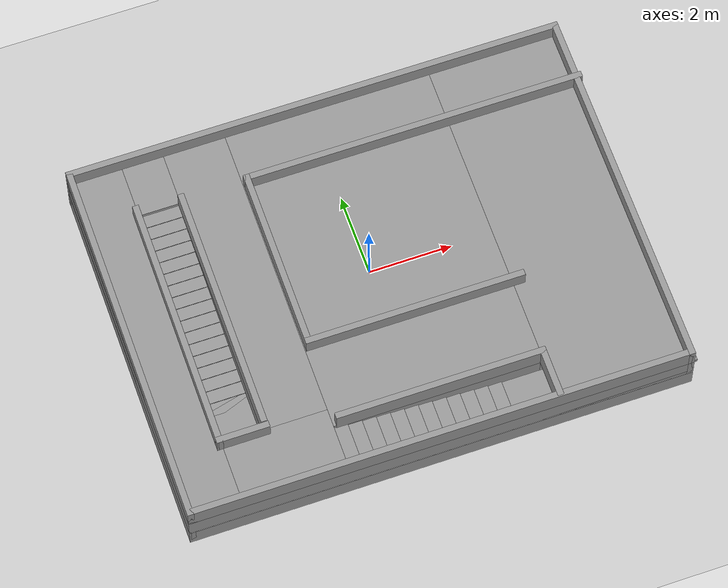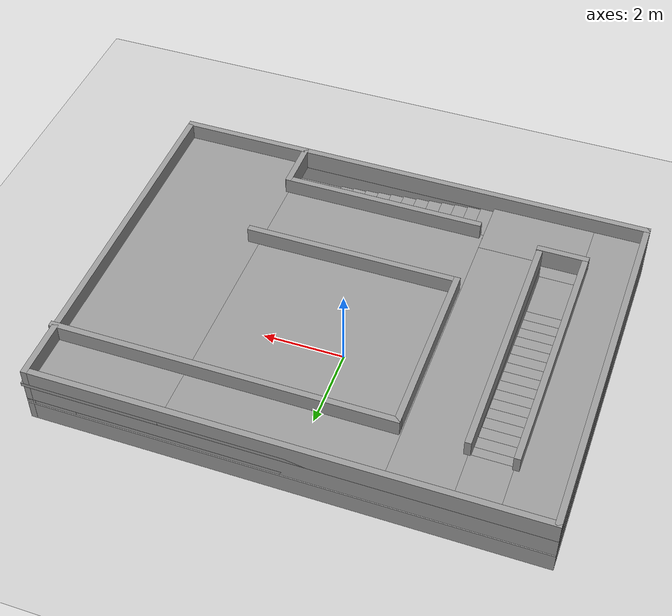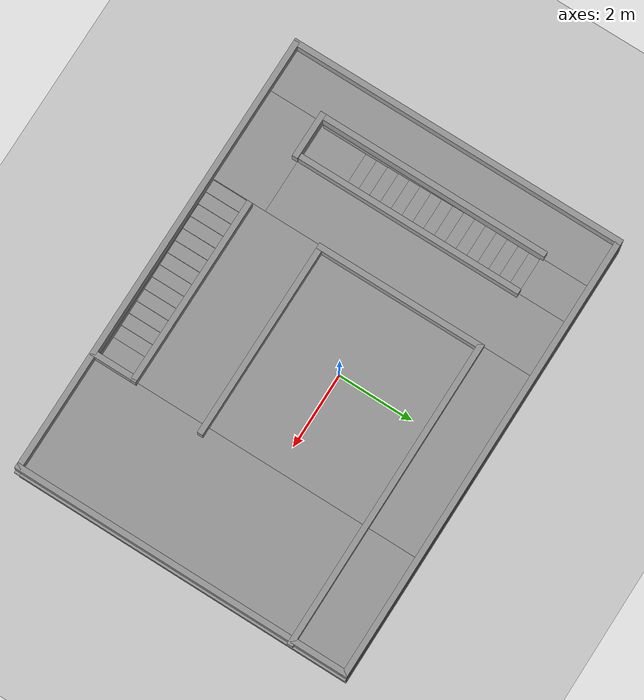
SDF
<sdf version="1.7">
 <world name="default">
  <light name="sun" type="directional">
   <pose>0 0 10 0 -0 0</pose>
   <diffuse>0.8 0.8 0.8 1</diffuse>
   <specular>0.2 0.2 0.2 1</specular>
   <attenuation>
    <range>1000</range>
    <constant>0.9</constant>
    <linear>0.01</linear>
    <quadratic>0.001</quadratic>
   </attenuation>
   <direction>-0.5 0.1 -0.9</direction>
   <spot><inner_angle>0</inner_angle><outer_angle>0</outer_angle><falloff>0</falloff></spot>
  </light>
  <model name="ground_plane">
   <static>1</static>
   <link name="link">
    <collision name="collision">
     <geometry><plane><normal>0 0 1</normal><size>100 100</size></plane></geometry>
     <surface>
      <contact><collide_bitmask>65535</collide_bitmask></contact>
      <friction><ode><mu>100</mu><mu2>50</mu2></ode></friction>
     </surface>
    </collision>
    <visual name="visual">
     <cast_shadows>0</cast_shadows>
     <geometry><plane><normal>0 0 1</normal><size>100 100</size></plane></geometry>
     <material>
      <script><uri>file://media/materials/scripts/gazebo.material</uri><name>Gazebo/Grey</name></script>
     </material>
    </visual>
   </link>
  </model>
  <gravity>0 0 -9.8</gravity>
  <magnetic_field>6e-06 2.3e-05 -4.2e-05</magnetic_field>
  <atmosphere type="adiabatic"/>
  <physics type="ode">
   <max_step_size>0.001</max_step_size>
   <real_time_factor>1</real_time_factor>
   <real_time_update_rate>1000</real_time_update_rate>
  </physics>
  <scene><ambient>0.4 0.4 0.4 1</ambient><background>0.7 0.7 0.7 1</background><shadows>1</shadows></scene>
  <spherical_coordinates>
   <surface_model>EARTH_WGS84</surface_model>
   <latitude_deg>0</latitude_deg>
   <longitude_deg>0</longitude_deg>
   <elevation>0</elevation>
   <heading_deg>0</heading_deg>
  </spherical_coordinates>
  <model name="builing1">
   <pose>0.045986 -0.516202 0 0 -0 0</pose>
   <link name="Floor_0">
    <pose>-0.031956 0 0.54 0 -0 0</pose>
    <visual name="Floor_0_Visual_0">
     <pose>-5.93283 0 0.05 0 -0 0</pose>
     <geometry><box><size>0.134333 9 0.1</size></box></geometry>
     <material>
      <script><uri>file://media/materials/scripts/gazebo.material</uri><name>Gazebo/Grey</name></script>
      <ambient>1 1 1 1</ambient>
     </material>
     <meta><layer>1</layer></meta>
    </visual>
    <collision name="Floor_0_Collision_0">
     <geometry><box><size>0.134333 9 0.1</size></box></geometry>
     <pose>-5.93283 0 0.05 0 -0 0</pose>
    </collision>
    <visual name="Floor_0_Visual_1">
     <pose>0.067166 -3.72455 0.05 0 -0 0</pose>
     <geometry><box><size>11.8657 1.5509 0.1</size></box></geometry>
     <material>
      <script><uri>file://media/materials/scripts/gazebo.material</uri><name>Gazebo/Grey</name></script>
      <ambient>1 1 1 1</ambient>
     </material>
     <meta><layer>1</layer></meta>
    </visual>
    <collision name="Floor_0_Collision_1">
     <geometry><box><size>11.8657 1.5509 0.1</size></box></geometry>
     <pose>0.067166 -3.72455 0.05 0 -0 0</pose>
    </collision>
    <visual name="Floor_0_Visual_2">
     <pose>-0.032905 0.77545 0.05 0 -0 0</pose>
     <geometry><box><size>9.66553 7.4491 0.1</size></box></geometry>
     <material>
      <script><uri>file://media/materials/scripts/gazebo.material</uri><name>Gazebo/Grey</name></script>
      <ambient>1 1 1 1</ambient>
     </material>
     <meta><layer>1</layer></meta>
    </visual>
    <collision name="Floor_0_Collision_2">
     <geometry><box><size>9.66553 7.4491 0.1</size></box></geometry>
     <pose>-0.032905 0.77545 0.05 0 -0 0</pose>
    </collision>
    <visual name="Floor_0_Visual_3">
     <pose>5.39993 -2.9298 0.05 0 -0 0</pose>
     <geometry><box><size>1.20014 0.038607 0.1</size></box></geometry>
     <material>
      <script><uri>file://media/materials/scripts/gazebo.material</uri><name>Gazebo/Grey</name></script>
      <ambient>1 1 1 1</ambient>
     </material>
     <meta><layer>1</layer></meta>
    </visual>
    <collision name="Floor_0_Collision_3">
     <geometry><box><size>1.20014 0.038607 0.1</size></box></geometry>
     <pose>5.39993 -2.9298 0.05 0 -0 0</pose>
    </collision>
    <visual name="Floor_0_Visual_4">
     <pose>5.89993 0.794754 0.05 0 -0 0</pose>
     <geometry><box><size>0.200142 7.41049 0.1</size></box></geometry>
     <material>
      <script><uri>file://media/materials/scripts/gazebo.material</uri><name>Gazebo/Grey</name></script>
      <ambient>1 1 1 1</ambient>
     </material>
     <meta><layer>1</layer></meta>
    </visual>
    <collision name="Floor_0_Collision_4">
     <geometry><box><size>0.200142 7.41049 0.1</size></box></geometry>
     <pose>5.89993 0.794754 0.05 0 -0 0</pose>
    </collision>
    <visual name="Floor_0_Visual_5">
     <pose>-5.36567 3.77545 0.05 0 -0 0</pose>
     <geometry><box><size>1 1.4491 0.1</size></box></geometry>
     <material>
      <script><uri>file://media/materials/scripts/gazebo.material</uri><name>Gazebo/Grey</name></script>
      <ambient>1 1 1 1</ambient>
     </material>
     <meta><layer>1</layer></meta>
    </visual>
    <collision name="Floor_0_Collision_5">
     <geometry><box><size>1 1.4491 0.1</size></box></geometry>
     <pose>-5.36567 3.77545 0.05 0 -0 0</pose>
    </collision>
    <visual name="Floor_0_Visual_6">
     <pose>5.29986 3.79475 0.05 0 -0 0</pose>
     <geometry><box><size>1 1.41049 0.1</size></box></geometry>
     <material>
      <script><uri>file://media/materials/scripts/gazebo.material</uri><name>Gazebo/Grey</name></script>
      <ambient>1 1 1 1</ambient>
     </material>
     <meta><layer>1</layer></meta>
    </visual>
    <collision name="Floor_0_Collision_6">
     <geometry><box><size>1 1.41049 0.1</size></box></geometry>
     <pose>5.29986 3.79475 0.05 0 -0 0</pose>
    </collision>
   </link>
   <link name="Floor_1">
    <pose>-4.5e-05 0 1.04 0 -0 0</pose>
    <visual name="Floor_1_Visual_0">
     <pose>-5.38471 0 0.05 0 -0 0</pose>
     <geometry><box><size>1.2944 9 0.1</size></box></geometry>
     <material>
      <script><uri>file://media/materials/scripts/gazebo.material</uri><name>Gazebo/Grey</name></script>
      <ambient>1 1 1 1</ambient>
     </material>
     <meta><layer>2</layer></meta>
    </visual>
    <collision name="Floor_1_Collision_0">
     <geometry><box><size>1.2944 9 0.1</size></box></geometry>
     <pose>-5.38471 0 0.05 0 -0 0</pose>
    </collision>
    <visual name="Floor_1_Visual_1">
     <pose>-3.48872 -3.70947 0.05 0 -0 0</pose>
     <geometry><box><size>2.49759 1.58106 0.1</size></box></geometry>
     <material>
      <script><uri>file://media/materials/scripts/gazebo.material</uri><name>Gazebo/Grey</name></script>
      <ambient>1 1 1 1</ambient>
     </material>
     <meta><layer>2</layer></meta>
    </visual>
    <collision name="Floor_1_Collision_1">
     <geometry><box><size>2.49759 1.58106 0.1</size></box></geometry>
     <pose>-3.48872 -3.70947 0.05 0 -0 0</pose>
    </collision>
    <visual name="Floor_1_Visual_2">
     <pose>1.89599 -4.42887 0.05 0 -0 0</pose>
     <geometry><box><size>8.27183 0.142252 0.1</size></box></geometry>
     <material>
      <script><uri>file://media/materials/scripts/gazebo.material</uri><name>Gazebo/Grey</name></script>
      <ambient>1 1 1 1</ambient>
     </material>
     <meta><layer>2</layer></meta>
    </visual>
    <collision name="Floor_1_Collision_2">
     <geometry><box><size>8.27183 0.142252 0.1</size></box></geometry>
     <pose>1.89599 -4.42887 0.05 0 -0 0</pose>
    </collision>
    <visual name="Floor_1_Visual_3">
     <pose>4.39599 0.071126 0.05 0 -0 0</pose>
     <geometry><box><size>3.27183 8.85775 0.1</size></box></geometry>
     <material>
      <script><uri>file://media/materials/scripts/gazebo.material</uri><name>Gazebo/Grey</name></script>
      <ambient>1 1 1 1</ambient>
     </material>
     <meta><layer>2</layer></meta>
    </visual>
    <collision name="Floor_1_Collision_3">
     <geometry><box><size>3.27183 8.85775 0.1</size></box></geometry>
     <pose>4.39599 0.071126 0.05 0 -0 0</pose>
    </collision>
    <visual name="Floor_1_Visual_4">
     <pose>0.260077 0.571126 0.05 0 -0 0</pose>
     <geometry><box><size>5 7.85775 0.1</size></box></geometry>
     <material>
      <script><uri>file://media/materials/scripts/gazebo.material</uri><name>Gazebo/Grey</name></script>
      <ambient>1 1 1 1</ambient>
     </material>
     <meta><layer>2</layer></meta>
    </visual>
    <collision name="Floor_1_Collision_4">
     <geometry><box><size>5 7.85775 0.1</size></box></geometry>
     <pose>0.260077 0.571126 0.05 0 -0 0</pose>
    </collision>
    <visual name="Floor_1_Visual_5">
     <pose>-2.98872 0.79053 0.05 0 -0 0</pose>
     <geometry><box><size>1.49759 7.41894 0.1</size></box></geometry>
     <material>
      <script><uri>file://media/materials/scripts/gazebo.material</uri><name>Gazebo/Grey</name></script>
      <ambient>1 1 1 1</ambient>
     </material>
     <meta><layer>2</layer></meta>
    </visual>
    <collision name="Floor_1_Collision_5">
     <geometry><box><size>1.49759 7.41894 0.1</size></box></geometry>
     <pose>-2.98872 0.79053 0.05 0 -0 0</pose>
    </collision>
    <visual name="Floor_1_Visual_6">
     <pose>-4.23751 3.79053 0.05 0 -0 0</pose>
     <geometry><box><size>1 1.41894 0.1</size></box></geometry>
     <material>
      <script><uri>file://media/materials/scripts/gazebo.material</uri><name>Gazebo/Grey</name></script>
      <ambient>1 1 1 1</ambient>
     </material>
     <meta><layer>2</layer></meta>
    </visual>
    <collision name="Floor_1_Collision_6">
     <geometry><box><size>1 1.41894 0.1</size></box></geometry>
     <pose>-4.23751 3.79053 0.05 0 -0 0</pose>
    </collision>
   </link>
   <link name="Stairs_1">
    <visual name="Stairs_1_Visual_0">
     <pose>-5.39762 2.9009 0.0125 0 -0 0</pose>
     <geometry><box><size>1 0.3 0.025</size></box></geometry>
     <material>
      <script><uri>file://media/materials/scripts/gazebo.material</uri><name>Gazebo/Grey</name></script>
      <ambient>1 1 1 1</ambient>
     </material>
     <meta><layer>0</layer></meta>
    </visual>
    <collision name="Stairs_1_Collision_0">
     <geometry><box><size>1 0.3 0.025</size></box></geometry>
     <pose>-5.39762 2.9009 0.0125 0 -0 0</pose>
    </collision>
    <visual name="Stairs_1_Visual_1">
     <pose>-5.39762 2.6009 0.0375 0 -0 0</pose>
     <geometry><box><size>1 0.3 0.025</size></box></geometry>
     <material>
      <script><uri>file://media/materials/scripts/gazebo.material</uri><name>Gazebo/Grey</name></script>
      <ambient>1 1 1 1</ambient>
     </material>
     <meta><layer>0</layer></meta>
    </visual>
    <collision name="Stairs_1_Collision_1">
     <geometry><box><size>1 0.3 0.025</size></box></geometry>
     <pose>-5.39762 2.6009 0.0375 0 -0 0</pose>
    </collision>
    <visual name="Stairs_1_Visual_2">
     <pose>-5.39762 2.3009 0.0625 0 -0 0</pose>
     <geometry><box><size>1 0.3 0.025</size></box></geometry>
     <material>
      <script><uri>file://media/materials/scripts/gazebo.material</uri><name>Gazebo/Grey</name></script>
      <ambient>1 1 1 1</ambient>
     </material>
     <meta><layer>0</layer></meta>
    </visual>
    <collision name="Stairs_1_Collision_2">
     <geometry><box><size>1 0.3 0.025</size></box></geometry>
     <pose>-5.39762 2.3009 0.0625 0 -0 0</pose>
    </collision>
    <visual name="Stairs_1_Visual_3">
     <pose>-5.39762 2.0009 0.0875 0 -0 0</pose>
     <geometry><box><size>1 0.3 0.025</size></box></geometry>
     <material>
      <script><uri>file://media/materials/scripts/gazebo.material</uri><name>Gazebo/Grey</name></script>
      <ambient>1 1 1 1</ambient>
     </material>
     <meta><layer>0</layer></meta>
    </visual>
    <collision name="Stairs_1_Collision_3">
     <geometry><box><size>1 0.3 0.025</size></box></geometry>
     <pose>-5.39762 2.0009 0.0875 0 -0 0</pose>
    </collision>
    <visual name="Stairs_1_Visual_4">
     <pose>-5.39762 1.7009 0.1125 0 -0 0</pose>
     <geometry><box><size>1 0.3 0.025</size></box></geometry>
     <material>
      <script><uri>file://media/materials/scripts/gazebo.material</uri><name>Gazebo/Grey</name></script>
      <ambient>1 1 1 1</ambient>
     </material>
     <meta><layer>0</layer></meta>
    </visual>
    <collision name="Stairs_1_Collision_4">
     <geometry><box><size>1 0.3 0.025</size></box></geometry>
     <pose>-5.39762 1.7009 0.1125 0 -0 0</pose>
    </collision>
    <visual name="Stairs_1_Visual_5">
     <pose>-5.39762 1.4009 0.1375 0 -0 0</pose>
     <geometry><box><size>1 0.3 0.025</size></box></geometry>
     <material>
      <script><uri>file://media/materials/scripts/gazebo.material</uri><name>Gazebo/Grey</name></script>
      <ambient>1 1 1 1</ambient>
     </material>
     <meta><layer>0</layer></meta>
    </visual>
    <collision name="Stairs_1_Collision_5">
     <geometry><box><size>1 0.3 0.025</size></box></geometry>
     <pose>-5.39762 1.4009 0.1375 0 -0 0</pose>
    </collision>
    <visual name="Stairs_1_Visual_6">
     <pose>-5.39762 1.1009 0.1625 0 -0 0</pose>
     <geometry><box><size>1 0.3 0.025</size></box></geometry>
     <material>
      <script><uri>file://media/materials/scripts/gazebo.material</uri><name>Gazebo/Grey</name></script>
      <ambient>1 1 1 1</ambient>
     </material>
     <meta><layer>0</layer></meta>
    </visual>
    <collision name="Stairs_1_Collision_6">
     <geometry><box><size>1 0.3 0.025</size></box></geometry>
     <pose>-5.39762 1.1009 0.1625 0 -0 0</pose>
    </collision>
    <visual name="Stairs_1_Visual_7">
     <pose>-5.39762 0.800901 0.1875 0 -0 0</pose>
     <geometry><box><size>1 0.3 0.025</size></box></geometry>
     <material>
      <script><uri>file://media/materials/scripts/gazebo.material</uri><name>Gazebo/Grey</name></script>
      <ambient>1 1 1 1</ambient>
     </material>
     <meta><layer>0</layer></meta>
    </visual>
    <collision name="Stairs_1_Collision_7">
     <geometry><box><size>1 0.3 0.025</size></box></geometry>
     <pose>-5.39762 0.800901 0.1875 0 -0 0</pose>
    </collision>
    <visual name="Stairs_1_Visual_8">
     <pose>-5.39762 0.500901 0.2125 0 -0 0</pose>
     <geometry><box><size>1 0.3 0.025</size></box></geometry>
     <material>
      <script><uri>file://media/materials/scripts/gazebo.material</uri><name>Gazebo/Grey</name></script>
      <ambient>1 1 1 1</ambient>
     </material>
     <meta><layer>0</layer></meta>
    </visual>
    <collision name="Stairs_1_Collision_8">
     <geometry><box><size>1 0.3 0.025</size></box></geometry>
     <pose>-5.39762 0.500901 0.2125 0 -0 0</pose>
    </collision>
    <visual name="Stairs_1_Visual_9">
     <pose>-5.39762 0.200901 0.2375 0 -0 0</pose>
     <geometry><box><size>1 0.3 0.025</size></box></geometry>
     <material>
      <script><uri>file://media/materials/scripts/gazebo.material</uri><name>Gazebo/Grey</name></script>
      <ambient>1 1 1 1</ambient>
     </material>
     <meta><layer>0</layer></meta>
    </visual>
    <collision name="Stairs_1_Collision_9">
     <geometry><box><size>1 0.3 0.025</size></box></geometry>
     <pose>-5.39762 0.200901 0.2375 0 -0 0</pose>
    </collision>
    <visual name="Stairs_1_Visual_10">
     <pose>-5.39762 -0.0991 0.2625 0 -0 0</pose>
     <geometry><box><size>1 0.3 0.025</size></box></geometry>
     <material>
      <script><uri>file://media/materials/scripts/gazebo.material</uri><name>Gazebo/Grey</name></script>
      <ambient>1 1 1 1</ambient>
     </material>
     <meta><layer>0</layer></meta>
    </visual>
    <collision name="Stairs_1_Collision_10">
     <geometry><box><size>1 0.3 0.025</size></box></geometry>
     <pose>-5.39762 -0.0991 0.2625 0 -0 0</pose>
    </collision>
    <visual name="Stairs_1_Visual_11">
     <pose>-5.39762 -0.399099 0.2875 0 -0 0</pose>
     <geometry><box><size>1 0.3 0.025</size></box></geometry>
     <material>
      <script><uri>file://media/materials/scripts/gazebo.material</uri><name>Gazebo/Grey</name></script>
      <ambient>1 1 1 1</ambient>
     </material>
     <meta><layer>0</layer></meta>
    </visual>
    <collision name="Stairs_1_Collision_11">
     <geometry><box><size>1 0.3 0.025</size></box></geometry>
     <pose>-5.39762 -0.399099 0.2875 0 -0 0</pose>
    </collision>
    <visual name="Stairs_1_Visual_12">
     <pose>-5.39762 -0.699099 0.3125 0 -0 0</pose>
     <geometry><box><size>1 0.3 0.025</size></box></geometry>
     <material>
      <script><uri>file://media/materials/scripts/gazebo.material</uri><name>Gazebo/Grey</name></script>
      <ambient>1 1 1 1</ambient>
     </material>
     <meta><layer>0</layer></meta>
    </visual>
    <collision name="Stairs_1_Collision_12">
     <geometry><box><size>1 0.3 0.025</size></box></geometry>
     <pose>-5.39762 -0.699099 0.3125 0 -0 0</pose>
    </collision>
    <visual name="Stairs_1_Visual_13">
     <pose>-5.39762 -0.999099 0.3375 0 -0 0</pose>
     <geometry><box><size>1 0.3 0.025</size></box></geometry>
     <material>
      <script><uri>file://media/materials/scripts/gazebo.material</uri><name>Gazebo/Grey</name></script>
      <ambient>1 1 1 1</ambient>
     </material>
     <meta><layer>0</layer></meta>
    </visual>
    <collision name="Stairs_1_Collision_13">
     <geometry><box><size>1 0.3 0.025</size></box></geometry>
     <pose>-5.39762 -0.999099 0.3375 0 -0 0</pose>
    </collision>
    <visual name="Stairs_1_Visual_14">
     <pose>-5.39762 -1.2991 0.3625 0 -0 0</pose>
     <geometry><box><size>1 0.3 0.025</size></box></geometry>
     <material>
      <script><uri>file://media/materials/scripts/gazebo.material</uri><name>Gazebo/Grey</name></script>
      <ambient>1 1 1 1</ambient>
     </material>
     <meta><layer>0</layer></meta>
    </visual>
    <collision name="Stairs_1_Collision_14">
     <geometry><box><size>1 0.3 0.025</size></box></geometry>
     <pose>-5.39762 -1.2991 0.3625 0 -0 0</pose>
    </collision>
    <visual name="Stairs_1_Visual_15">
     <pose>-5.39762 -1.5991 0.3875 0 -0 0</pose>
     <geometry><box><size>1 0.3 0.025</size></box></geometry>
     <material>
      <script><uri>file://media/materials/scripts/gazebo.material</uri><name>Gazebo/Grey</name></script>
      <ambient>1 1 1 1</ambient>
     </material>
     <meta><layer>0</layer></meta>
    </visual>
    <collision name="Stairs_1_Collision_15">
     <geometry><box><size>1 0.3 0.025</size></box></geometry>
     <pose>-5.39762 -1.5991 0.3875 0 -0 0</pose>
    </collision>
    <visual name="Stairs_1_Visual_16">
     <pose>-5.39762 -1.8991 0.4125 0 -0 0</pose>
     <geometry><box><size>1 0.3 0.025</size></box></geometry>
     <material>
      <script><uri>file://media/materials/scripts/gazebo.material</uri><name>Gazebo/Grey</name></script>
      <ambient>1 1 1 1</ambient>
     </material>
     <meta><layer>0</layer></meta>
    </visual>
    <collision name="Stairs_1_Collision_16">
     <geometry><box><size>1 0.3 0.025</size></box></geometry>
     <pose>-5.39762 -1.8991 0.4125 0 -0 0</pose>
    </collision>
    <visual name="Stairs_1_Visual_17">
     <pose>-5.39762 -2.1991 0.4375 0 -0 0</pose>
     <geometry><box><size>1 0.3 0.025</size></box></geometry>
     <material>
      <script><uri>file://media/materials/scripts/gazebo.material</uri><name>Gazebo/Grey</name></script>
      <ambient>1 1 1 1</ambient>
     </material>
     <meta><layer>0</layer></meta>
    </visual>
    <collision name="Stairs_1_Collision_17">
     <geometry><box><size>1 0.3 0.025</size></box></geometry>
     <pose>-5.39762 -2.1991 0.4375 0 -0 0</pose>
    </collision>
    <visual name="Stairs_1_Visual_18">
     <pose>-5.39762 -2.4991 0.4625 0 -0 0</pose>
     <geometry><box><size>1 0.3 0.025</size></box></geometry>
     <material>
      <script><uri>file://media/materials/scripts/gazebo.material</uri><name>Gazebo/Grey</name></script>
      <ambient>1 1 1 1</ambient>
     </material>
     <meta><layer>0</layer></meta>
    </visual>
    <collision name="Stairs_1_Collision_18">
     <geometry><box><size>1 0.3 0.025</size></box></geometry>
     <pose>-5.39762 -2.4991 0.4625 0 -0 0</pose>
    </collision>
    <visual name="Stairs_1_Visual_19">
     <pose>-5.39762 -2.7991 0.4875 0 -0 0</pose>
     <geometry><box><size>1 0.3 0.025</size></box></geometry>
     <material>
      <script><uri>file://media/materials/scripts/gazebo.material</uri><name>Gazebo/Grey</name></script>
      <ambient>1 1 1 1</ambient>
     </material>
     <meta><layer>0</layer></meta>
    </visual>
    <collision name="Stairs_1_Collision_19">
     <geometry><box><size>1 0.3 0.025</size></box></geometry>
     <pose>-5.39762 -2.7991 0.4875 0 -0 0</pose>
    </collision>
   </link>
   <link name="Stairs_3">
    <visual name="Stairs_3_Visual_0">
     <pose>5.2679 -2.76049 0.0125 0 -0 -3.14159</pose>
     <geometry><box><size>1 0.3 0.025</size></box></geometry>
     <material>
      <script><uri>file://media/materials/scripts/gazebo.material</uri><name>Gazebo/Grey</name></script>
      <ambient>1 1 1 1</ambient>
     </material>
     <meta><layer>0</layer></meta>
    </visual>
    <collision name="Stairs_3_Collision_0">
     <geometry><box><size>1 0.3 0.025</size></box></geometry>
     <pose>5.2679 -2.76049 0.0125 0 -0 -3.14159</pose>
    </collision>
    <visual name="Stairs_3_Visual_1">
     <pose>5.2679 -2.46049 0.0375 0 -0 -3.14159</pose>
     <geometry><box><size>1 0.3 0.025</size></box></geometry>
     <material>
      <script><uri>file://media/materials/scripts/gazebo.material</uri><name>Gazebo/Grey</name></script>
      <ambient>1 1 1 1</ambient>
     </material>
     <meta><layer>0</layer></meta>
    </visual>
    <collision name="Stairs_3_Collision_1">
     <geometry><box><size>1 0.3 0.025</size></box></geometry>
     <pose>5.2679 -2.46049 0.0375 0 -0 -3.14159</pose>
    </collision>
    <visual name="Stairs_3_Visual_2">
     <pose>5.2679 -2.16049 0.0625 0 -0 -3.14159</pose>
     <geometry><box><size>1 0.3 0.025</size></box></geometry>
     <material>
      <script><uri>file://media/materials/scripts/gazebo.material</uri><name>Gazebo/Grey</name></script>
      <ambient>1 1 1 1</ambient>
     </material>
     <meta><layer>0</layer></meta>
    </visual>
    <collision name="Stairs_3_Collision_2">
     <geometry><box><size>1 0.3 0.025</size></box></geometry>
     <pose>5.2679 -2.16049 0.0625 0 -0 -3.14159</pose>
    </collision>
    <visual name="Stairs_3_Visual_3">
     <pose>5.2679 -1.86049 0.0875 0 -0 -3.14159</pose>
     <geometry><box><size>1 0.3 0.025</size></box></geometry>
     <material>
      <script><uri>file://media/materials/scripts/gazebo.material</uri><name>Gazebo/Grey</name></script>
      <ambient>1 1 1 1</ambient>
     </material>
     <meta><layer>0</layer></meta>
    </visual>
    <collision name="Stairs_3_Collision_3">
     <geometry><box><size>1 0.3 0.025</size></box></geometry>
     <pose>5.2679 -1.86049 0.0875 0 -0 -3.14159</pose>
    </collision>
    <visual name="Stairs_3_Visual_4">
     <pose>5.2679 -1.56049 0.1125 0 -0 -3.14159</pose>
     <geometry><box><size>1 0.3 0.025</size></box></geometry>
     <material>
      <script><uri>file://media/materials/scripts/gazebo.material</uri><name>Gazebo/Grey</name></script>
      <ambient>1 1 1 1</ambient>
     </material>
     <meta><layer>0</layer></meta>
    </visual>
    <collision name="Stairs_3_Collision_4">
     <geometry><box><size>1 0.3 0.025</size></box></geometry>
     <pose>5.2679 -1.56049 0.1125 0 -0 -3.14159</pose>
    </collision>
    <visual name="Stairs_3_Visual_5">
     <pose>5.2679 -1.26049 0.1375 0 -0 -3.14159</pose>
     <geometry><box><size>1 0.3 0.025</size></box></geometry>
     <material>
      <script><uri>file://media/materials/scripts/gazebo.material</uri><name>Gazebo/Grey</name></script>
      <ambient>1 1 1 1</ambient>
     </material>
     <meta><layer>0</layer></meta>
    </visual>
    <collision name="Stairs_3_Collision_5">
     <geometry><box><size>1 0.3 0.025</size></box></geometry>
     <pose>5.2679 -1.26049 0.1375 0 -0 -3.14159</pose>
    </collision>
    <visual name="Stairs_3_Visual_6">
     <pose>5.2679 -0.960492 0.1625 0 -0 -3.14159</pose>
     <geometry><box><size>1 0.3 0.025</size></box></geometry>
     <material>
      <script><uri>file://media/materials/scripts/gazebo.material</uri><name>Gazebo/Grey</name></script>
      <ambient>1 1 1 1</ambient>
     </material>
     <meta><layer>0</layer></meta>
    </visual>
    <collision name="Stairs_3_Collision_6">
     <geometry><box><size>1 0.3 0.025</size></box></geometry>
     <pose>5.2679 -0.960492 0.1625 0 -0 -3.14159</pose>
    </collision>
    <visual name="Stairs_3_Visual_7">
     <pose>5.2679 -0.660492 0.1875 0 -0 -3.14159</pose>
     <geometry><box><size>1 0.3 0.025</size></box></geometry>
     <material>
      <script><uri>file://media/materials/scripts/gazebo.material</uri><name>Gazebo/Grey</name></script>
      <ambient>1 1 1 1</ambient>
     </material>
     <meta><layer>0</layer></meta>
    </visual>
    <collision name="Stairs_3_Collision_7">
     <geometry><box><size>1 0.3 0.025</size></box></geometry>
     <pose>5.2679 -0.660492 0.1875 0 -0 -3.14159</pose>
    </collision>
    <visual name="Stairs_3_Visual_8">
     <pose>5.2679 -0.360492 0.2125 0 -0 -3.14159</pose>
     <geometry><box><size>1 0.3 0.025</size></box></geometry>
     <material>
      <script><uri>file://media/materials/scripts/gazebo.material</uri><name>Gazebo/Grey</name></script>
      <ambient>1 1 1 1</ambient>
     </material>
     <meta><layer>0</layer></meta>
    </visual>
    <collision name="Stairs_3_Collision_8">
     <geometry><box><size>1 0.3 0.025</size></box></geometry>
     <pose>5.2679 -0.360492 0.2125 0 -0 -3.14159</pose>
    </collision>
    <visual name="Stairs_3_Visual_9">
     <pose>5.2679 -0.060492 0.2375 0 -0 -3.14159</pose>
     <geometry><box><size>1 0.3 0.025</size></box></geometry>
     <material>
      <script><uri>file://media/materials/scripts/gazebo.material</uri><name>Gazebo/Grey</name></script>
      <ambient>1 1 1 1</ambient>
     </material>
     <meta><layer>0</layer></meta>
    </visual>
    <collision name="Stairs_3_Collision_9">
     <geometry><box><size>1 0.3 0.025</size></box></geometry>
     <pose>5.2679 -0.060492 0.2375 0 -0 -3.14159</pose>
    </collision>
    <visual name="Stairs_3_Visual_10">
     <pose>5.2679 0.239508 0.2625 0 -0 -3.14159</pose>
     <geometry><box><size>1 0.3 0.025</size></box></geometry>
     <material>
      <script><uri>file://media/materials/scripts/gazebo.material</uri><name>Gazebo/Grey</name></script>
      <ambient>1 1 1 1</ambient>
     </material>
     <meta><layer>0</layer></meta>
    </visual>
    <collision name="Stairs_3_Collision_10">
     <geometry><box><size>1 0.3 0.025</size></box></geometry>
     <pose>5.2679 0.239508 0.2625 0 -0 -3.14159</pose>
    </collision>
    <visual name="Stairs_3_Visual_11">
     <pose>5.2679 0.539508 0.2875 0 -0 -3.14159</pose>
     <geometry><box><size>1 0.3 0.025</size></box></geometry>
     <material>
      <script><uri>file://media/materials/scripts/gazebo.material</uri><name>Gazebo/Grey</name></script>
      <ambient>1 1 1 1</ambient>
     </material>
     <meta><layer>0</layer></meta>
    </visual>
    <collision name="Stairs_3_Collision_11">
     <geometry><box><size>1 0.3 0.025</size></box></geometry>
     <pose>5.2679 0.539508 0.2875 0 -0 -3.14159</pose>
    </collision>
    <visual name="Stairs_3_Visual_12">
     <pose>5.2679 0.839508 0.3125 0 -0 -3.14159</pose>
     <geometry><box><size>1 0.3 0.025</size></box></geometry>
     <material>
      <script><uri>file://media/materials/scripts/gazebo.material</uri><name>Gazebo/Grey</name></script>
      <ambient>1 1 1 1</ambient>
     </material>
     <meta><layer>0</layer></meta>
    </visual>
    <collision name="Stairs_3_Collision_12">
     <geometry><box><size>1 0.3 0.025</size></box></geometry>
     <pose>5.2679 0.839508 0.3125 0 -0 -3.14159</pose>
    </collision>
    <visual name="Stairs_3_Visual_13">
     <pose>5.2679 1.13951 0.3375 0 -0 -3.14159</pose>
     <geometry><box><size>1 0.3 0.025</size></box></geometry>
     <material>
      <script><uri>file://media/materials/scripts/gazebo.material</uri><name>Gazebo/Grey</name></script>
      <ambient>1 1 1 1</ambient>
     </material>
     <meta><layer>0</layer></meta>
    </visual>
    <collision name="Stairs_3_Collision_13">
     <geometry><box><size>1 0.3 0.025</size></box></geometry>
     <pose>5.2679 1.13951 0.3375 0 -0 -3.14159</pose>
    </collision>
    <visual name="Stairs_3_Visual_14">
     <pose>5.2679 1.43951 0.3625 0 -0 -3.14159</pose>
     <geometry><box><size>1 0.3 0.025</size></box></geometry>
     <material>
      <script><uri>file://media/materials/scripts/gazebo.material</uri><name>Gazebo/Grey</name></script>
      <ambient>1 1 1 1</ambient>
     </material>
     <meta><layer>0</layer></meta>
    </visual>
    <collision name="Stairs_3_Collision_14">
     <geometry><box><size>1 0.3 0.025</size></box></geometry>
     <pose>5.2679 1.43951 0.3625 0 -0 -3.14159</pose>
    </collision>
    <visual name="Stairs_3_Visual_15">
     <pose>5.2679 1.73951 0.3875 0 -0 -3.14159</pose>
     <geometry><box><size>1 0.3 0.025</size></box></geometry>
     <material>
      <script><uri>file://media/materials/scripts/gazebo.material</uri><name>Gazebo/Grey</name></script>
      <ambient>1 1 1 1</ambient>
     </material>
     <meta><layer>0</layer></meta>
    </visual>
    <collision name="Stairs_3_Collision_15">
     <geometry><box><size>1 0.3 0.025</size></box></geometry>
     <pose>5.2679 1.73951 0.3875 0 -0 -3.14159</pose>
    </collision>
    <visual name="Stairs_3_Visual_16">
     <pose>5.2679 2.03951 0.4125 0 -0 -3.14159</pose>
     <geometry><box><size>1 0.3 0.025</size></box></geometry>
     <material>
      <script><uri>file://media/materials/scripts/gazebo.material</uri><name>Gazebo/Grey</name></script>
      <ambient>1 1 1 1</ambient>
     </material>
     <meta><layer>0</layer></meta>
    </visual>
    <collision name="Stairs_3_Collision_16">
     <geometry><box><size>1 0.3 0.025</size></box></geometry>
     <pose>5.2679 2.03951 0.4125 0 -0 -3.14159</pose>
    </collision>
    <visual name="Stairs_3_Visual_17">
     <pose>5.2679 2.33951 0.4375 0 -0 -3.14159</pose>
     <geometry><box><size>1 0.3 0.025</size></box></geometry>
     <material>
      <script><uri>file://media/materials/scripts/gazebo.material</uri><name>Gazebo/Grey</name></script>
      <ambient>1 1 1 1</ambient>
     </material>
     <meta><layer>0</layer></meta>
    </visual>
    <collision name="Stairs_3_Collision_17">
     <geometry><box><size>1 0.3 0.025</size></box></geometry>
     <pose>5.2679 2.33951 0.4375 0 -0 -3.14159</pose>
    </collision>
    <visual name="Stairs_3_Visual_18">
     <pose>5.2679 2.63951 0.4625 0 -0 -3.14159</pose>
     <geometry><box><size>1 0.3 0.025</size></box></geometry>
     <material>
      <script><uri>file://media/materials/scripts/gazebo.material</uri><name>Gazebo/Grey</name></script>
      <ambient>1 1 1 1</ambient>
     </material>
     <meta><layer>0</layer></meta>
    </visual>
    <collision name="Stairs_3_Collision_18">
     <geometry><box><size>1 0.3 0.025</size></box></geometry>
     <pose>5.2679 2.63951 0.4625 0 -0 -3.14159</pose>
    </collision>
    <visual name="Stairs_3_Visual_19">
     <pose>5.2679 2.93951 0.4875 0 -0 -3.14159</pose>
     <geometry><box><size>1 0.3 0.025</size></box></geometry>
     <material>
      <script><uri>file://media/materials/scripts/gazebo.material</uri><name>Gazebo/Grey</name></script>
      <ambient>1 1 1 1</ambient>
     </material>
     <meta><layer>0</layer></meta>
    </visual>
    <collision name="Stairs_3_Collision_19">
     <geometry><box><size>1 0.3 0.025</size></box></geometry>
     <pose>5.2679 2.93951 0.4875 0 -0 -3.14159</pose>
    </collision>
   </link>
   <link name="Stairs_5">
    <visual name="Stairs_5_Visual_0">
     <pose>-4.23756 -2.76894 0.5525 0 -0 -3.14159</pose>
     <geometry><box><size>1 0.3 0.025</size></box></geometry>
     <material>
      <script><uri>file://media/materials/scripts/gazebo.material</uri><name>Gazebo/Grey</name></script>
      <ambient>1 1 1 1</ambient>
     </material>
     <meta><layer>1</layer></meta>
    </visual>
    <collision name="Stairs_5_Collision_0">
     <geometry><box><size>1 0.3 0.025</size></box></geometry>
     <pose>-4.23756 -2.76894 0.5525 0 -0 -3.14159</pose>
    </collision>
    <visual name="Stairs_5_Visual_1">
     <pose>-4.23756 -2.46894 0.5775 0 -0 -3.14159</pose>
     <geometry><box><size>1 0.3 0.025</size></box></geometry>
     <material>
      <script><uri>file://media/materials/scripts/gazebo.material</uri><name>Gazebo/Grey</name></script>
      <ambient>1 1 1 1</ambient>
     </material>
     <meta><layer>1</layer></meta>
    </visual>
    <collision name="Stairs_5_Collision_1">
     <geometry><box><size>1 0.3 0.025</size></box></geometry>
     <pose>-4.23756 -2.46894 0.5775 0 -0 -3.14159</pose>
    </collision>
    <visual name="Stairs_5_Visual_2">
     <pose>-4.23756 -2.16894 0.6025 0 -0 -3.14159</pose>
     <geometry><box><size>1 0.3 0.025</size></box></geometry>
     <material>
      <script><uri>file://media/materials/scripts/gazebo.material</uri><name>Gazebo/Grey</name></script>
      <ambient>1 1 1 1</ambient>
     </material>
     <meta><layer>1</layer></meta>
    </visual>
    <collision name="Stairs_5_Collision_2">
     <geometry><box><size>1 0.3 0.025</size></box></geometry>
     <pose>-4.23756 -2.16894 0.6025 0 -0 -3.14159</pose>
    </collision>
    <visual name="Stairs_5_Visual_3">
     <pose>-4.23756 -1.86894 0.6275 0 -0 -3.14159</pose>
     <geometry><box><size>1 0.3 0.025</size></box></geometry>
     <material>
      <script><uri>file://media/materials/scripts/gazebo.material</uri><name>Gazebo/Grey</name></script>
      <ambient>1 1 1 1</ambient>
     </material>
     <meta><layer>1</layer></meta>
    </visual>
    <collision name="Stairs_5_Collision_3">
     <geometry><box><size>1 0.3 0.025</size></box></geometry>
     <pose>-4.23756 -1.86894 0.6275 0 -0 -3.14159</pose>
    </collision>
    <visual name="Stairs_5_Visual_4">
     <pose>-4.23756 -1.56894 0.6525 0 -0 -3.14159</pose>
     <geometry><box><size>1 0.3 0.025</size></box></geometry>
     <material>
      <script><uri>file://media/materials/scripts/gazebo.material</uri><name>Gazebo/Grey</name></script>
      <ambient>1 1 1 1</ambient>
     </material>
     <meta><layer>1</layer></meta>
    </visual>
    <collision name="Stairs_5_Collision_4">
     <geometry><box><size>1 0.3 0.025</size></box></geometry>
     <pose>-4.23756 -1.56894 0.6525 0 -0 -3.14159</pose>
    </collision>
    <visual name="Stairs_5_Visual_5">
     <pose>-4.23756 -1.26894 0.6775 0 -0 -3.14159</pose>
     <geometry><box><size>1 0.3 0.025</size></box></geometry>
     <material>
      <script><uri>file://media/materials/scripts/gazebo.material</uri><name>Gazebo/Grey</name></script>
      <ambient>1 1 1 1</ambient>
     </material>
     <meta><layer>1</layer></meta>
    </visual>
    <collision name="Stairs_5_Collision_5">
     <geometry><box><size>1 0.3 0.025</size></box></geometry>
     <pose>-4.23756 -1.26894 0.6775 0 -0 -3.14159</pose>
    </collision>
    <visual name="Stairs_5_Visual_6">
     <pose>-4.23756 -0.96894 0.7025 0 -0 -3.14159</pose>
     <geometry><box><size>1 0.3 0.025</size></box></geometry>
     <material>
      <script><uri>file://media/materials/scripts/gazebo.material</uri><name>Gazebo/Grey</name></script>
      <ambient>1 1 1 1</ambient>
     </material>
     <meta><layer>1</layer></meta>
    </visual>
    <collision name="Stairs_5_Collision_6">
     <geometry><box><size>1 0.3 0.025</size></box></geometry>
     <pose>-4.23756 -0.96894 0.7025 0 -0 -3.14159</pose>
    </collision>
    <visual name="Stairs_5_Visual_7">
     <pose>-4.23756 -0.66894 0.7275 0 -0 -3.14159</pose>
     <geometry><box><size>1 0.3 0.025</size></box></geometry>
     <material>
      <script><uri>file://media/materials/scripts/gazebo.material</uri><name>Gazebo/Grey</name></script>
      <ambient>1 1 1 1</ambient>
     </material>
     <meta><layer>1</layer></meta>
    </visual>
    <collision name="Stairs_5_Collision_7">
     <geometry><box><size>1 0.3 0.025</size></box></geometry>
     <pose>-4.23756 -0.66894 0.7275 0 -0 -3.14159</pose>
    </collision>
    <visual name="Stairs_5_Visual_8">
     <pose>-4.23756 -0.36894 0.7525 0 -0 -3.14159</pose>
     <geometry><box><size>1 0.3 0.025</size></box></geometry>
     <material>
      <script><uri>file://media/materials/scripts/gazebo.material</uri><name>Gazebo/Grey</name></script>
      <ambient>1 1 1 1</ambient>
     </material>
     <meta><layer>1</layer></meta>
    </visual>
    <collision name="Stairs_5_Collision_8">
     <geometry><box><size>1 0.3 0.025</size></box></geometry>
     <pose>-4.23756 -0.36894 0.7525 0 -0 -3.14159</pose>
    </collision>
    <visual name="Stairs_5_Visual_9">
     <pose>-4.23756 -0.06894 0.7775 0 -0 -3.14159</pose>
     <geometry><box><size>1 0.3 0.025</size></box></geometry>
     <material>
      <script><uri>file://media/materials/scripts/gazebo.material</uri><name>Gazebo/Grey</name></script>
      <ambient>1 1 1 1</ambient>
     </material>
     <meta><layer>1</layer></meta>
    </visual>
    <collision name="Stairs_5_Collision_9">
     <geometry><box><size>1 0.3 0.025</size></box></geometry>
     <pose>-4.23756 -0.06894 0.7775 0 -0 -3.14159</pose>
    </collision>
    <visual name="Stairs_5_Visual_10">
     <pose>-4.23756 0.23106 0.8025 0 -0 -3.14159</pose>
     <geometry><box><size>1 0.3 0.025</size></box></geometry>
     <material>
      <script><uri>file://media/materials/scripts/gazebo.material</uri><name>Gazebo/Grey</name></script>
      <ambient>1 1 1 1</ambient>
     </material>
     <meta><layer>1</layer></meta>
    </visual>
    <collision name="Stairs_5_Collision_10">
     <geometry><box><size>1 0.3 0.025</size></box></geometry>
     <pose>-4.23756 0.23106 0.8025 0 -0 -3.14159</pose>
    </collision>
    <visual name="Stairs_5_Visual_11">
     <pose>-4.23756 0.53106 0.8275 0 -0 -3.14159</pose>
     <geometry><box><size>1 0.3 0.025</size></box></geometry>
     <material>
      <script><uri>file://media/materials/scripts/gazebo.material</uri><name>Gazebo/Grey</name></script>
      <ambient>1 1 1 1</ambient>
     </material>
     <meta><layer>1</layer></meta>
    </visual>
    <collision name="Stairs_5_Collision_11">
     <geometry><box><size>1 0.3 0.025</size></box></geometry>
     <pose>-4.23756 0.53106 0.8275 0 -0 -3.14159</pose>
    </collision>
    <visual name="Stairs_5_Visual_12">
     <pose>-4.23756 0.83106 0.8525 0 -0 -3.14159</pose>
     <geometry><box><size>1 0.3 0.025</size></box></geometry>
     <material>
      <script><uri>file://media/materials/scripts/gazebo.material</uri><name>Gazebo/Grey</name></script>
      <ambient>1 1 1 1</ambient>
     </material>
     <meta><layer>1</layer></meta>
    </visual>
    <collision name="Stairs_5_Collision_12">
     <geometry><box><size>1 0.3 0.025</size></box></geometry>
     <pose>-4.23756 0.83106 0.8525 0 -0 -3.14159</pose>
    </collision>
    <visual name="Stairs_5_Visual_13">
     <pose>-4.23756 1.13106 0.8775 0 -0 -3.14159</pose>
     <geometry><box><size>1 0.3 0.025</size></box></geometry>
     <material>
      <script><uri>file://media/materials/scripts/gazebo.material</uri><name>Gazebo/Grey</name></script>
      <ambient>1 1 1 1</ambient>
     </material>
     <meta><layer>1</layer></meta>
    </visual>
    <collision name="Stairs_5_Collision_13">
     <geometry><box><size>1 0.3 0.025</size></box></geometry>
     <pose>-4.23756 1.13106 0.8775 0 -0 -3.14159</pose>
    </collision>
    <visual name="Stairs_5_Visual_14">
     <pose>-4.23756 1.43106 0.9025 0 -0 -3.14159</pose>
     <geometry><box><size>1 0.3 0.025</size></box></geometry>
     <material>
      <script><uri>file://media/materials/scripts/gazebo.material</uri><name>Gazebo/Grey</name></script>
      <ambient>1 1 1 1</ambient>
     </material>
     <meta><layer>1</layer></meta>
    </visual>
    <collision name="Stairs_5_Collision_14">
     <geometry><box><size>1 0.3 0.025</size></box></geometry>
     <pose>-4.23756 1.43106 0.9025 0 -0 -3.14159</pose>
    </collision>
    <visual name="Stairs_5_Visual_15">
     <pose>-4.23756 1.73106 0.9275 0 -0 -3.14159</pose>
     <geometry><box><size>1 0.3 0.025</size></box></geometry>
     <material>
      <script><uri>file://media/materials/scripts/gazebo.material</uri><name>Gazebo/Grey</name></script>
      <ambient>1 1 1 1</ambient>
     </material>
     <meta><layer>1</layer></meta>
    </visual>
    <collision name="Stairs_5_Collision_15">
     <geometry><box><size>1 0.3 0.025</size></box></geometry>
     <pose>-4.23756 1.73106 0.9275 0 -0 -3.14159</pose>
    </collision>
    <visual name="Stairs_5_Visual_16">
     <pose>-4.23756 2.03106 0.9525 0 -0 -3.14159</pose>
     <geometry><box><size>1 0.3 0.025</size></box></geometry>
     <material>
      <script><uri>file://media/materials/scripts/gazebo.material</uri><name>Gazebo/Grey</name></script>
      <ambient>1 1 1 1</ambient>
     </material>
     <meta><layer>1</layer></meta>
    </visual>
    <collision name="Stairs_5_Collision_16">
     <geometry><box><size>1 0.3 0.025</size></box></geometry>
     <pose>-4.23756 2.03106 0.9525 0 -0 -3.14159</pose>
    </collision>
    <visual name="Stairs_5_Visual_17">
     <pose>-4.23756 2.33106 0.9775 0 -0 -3.14159</pose>
     <geometry><box><size>1 0.3 0.025</size></box></geometry>
     <material>
      <script><uri>file://media/materials/scripts/gazebo.material</uri><name>Gazebo/Grey</name></script>
      <ambient>1 1 1 1</ambient>
     </material>
     <meta><layer>1</layer></meta>
    </visual>
    <collision name="Stairs_5_Collision_17">
     <geometry><box><size>1 0.3 0.025</size></box></geometry>
     <pose>-4.23756 2.33106 0.9775 0 -0 -3.14159</pose>
    </collision>
    <visual name="Stairs_5_Visual_18">
     <pose>-4.23756 2.63106 1.0025 0 -0 -3.14159</pose>
     <geometry><box><size>1 0.3 0.025</size></box></geometry>
     <material>
      <script><uri>file://media/materials/scripts/gazebo.material</uri><name>Gazebo/Grey</name></script>
      <ambient>1 1 1 1</ambient>
     </material>
     <meta><layer>1</layer></meta>
    </visual>
    <collision name="Stairs_5_Collision_18">
     <geometry><box><size>1 0.3 0.025</size></box></geometry>
     <pose>-4.23756 2.63106 1.0025 0 -0 -3.14159</pose>
    </collision>
    <visual name="Stairs_5_Visual_19">
     <pose>-4.23756 2.93106 1.0275 0 -0 -3.14159</pose>
     <geometry><box><size>1 0.3 0.025</size></box></geometry>
     <material>
      <script><uri>file://media/materials/scripts/gazebo.material</uri><name>Gazebo/Grey</name></script>
      <ambient>1 1 1 1</ambient>
     </material>
     <meta><layer>1</layer></meta>
    </visual>
    <collision name="Stairs_5_Collision_19">
     <geometry><box><size>1 0.3 0.025</size></box></geometry>
     <pose>-4.23756 2.93106 1.0275 0 -0 -3.14159</pose>
    </collision>
   </link>
   <link name="Stairs_6">
    <visual name="Stairs_6_Visual_0">
     <pose>2.59337 -3.85775 0.556667 0 -0 -1.5708</pose>
     <geometry><box><size>1 0.333333 0.033333</size></box></geometry>
     <material>
      <script><uri>file://media/materials/scripts/gazebo.material</uri><name>Gazebo/Grey</name></script>
      <ambient>1 1 1 1</ambient>
     </material>
     <meta><layer>1</layer></meta>
    </visual>
    <collision name="Stairs_6_Collision_0">
     <geometry><box><size>1 0.333333 0.033333</size></box></geometry>
     <pose>2.59337 -3.85775 0.556667 0 -0 -1.5708</pose>
    </collision>
    <visual name="Stairs_6_Visual_1">
     <pose>2.26003 -3.85775 0.59 0 -0 -1.5708</pose>
     <geometry><box><size>1 0.333333 0.033333</size></box></geometry>
     <material>
      <script><uri>file://media/materials/scripts/gazebo.material</uri><name>Gazebo/Grey</name></script>
      <ambient>1 1 1 1</ambient>
     </material>
     <meta><layer>1</layer></meta>
    </visual>
    <collision name="Stairs_6_Collision_1">
     <geometry><box><size>1 0.333333 0.033333</size></box></geometry>
     <pose>2.26003 -3.85775 0.59 0 -0 -1.5708</pose>
    </collision>
    <visual name="Stairs_6_Visual_2">
     <pose>1.9267 -3.85775 0.623333 0 -0 -1.5708</pose>
     <geometry><box><size>1 0.333333 0.033333</size></box></geometry>
     <material>
      <script><uri>file://media/materials/scripts/gazebo.material</uri><name>Gazebo/Grey</name></script>
      <ambient>1 1 1 1</ambient>
     </material>
     <meta><layer>1</layer></meta>
    </visual>
    <collision name="Stairs_6_Collision_2">
     <geometry><box><size>1 0.333333 0.033333</size></box></geometry>
     <pose>1.9267 -3.85775 0.623333 0 -0 -1.5708</pose>
    </collision>
    <visual name="Stairs_6_Visual_3">
     <pose>1.59336 -3.85775 0.656667 0 -0 -1.5708</pose>
     <geometry><box><size>1 0.333333 0.033333</size></box></geometry>
     <material>
      <script><uri>file://media/materials/scripts/gazebo.material</uri><name>Gazebo/Grey</name></script>
      <ambient>1 1 1 1</ambient>
     </material>
     <meta><layer>1</layer></meta>
    </visual>
    <collision name="Stairs_6_Collision_3">
     <geometry><box><size>1 0.333333 0.033333</size></box></geometry>
     <pose>1.59336 -3.85775 0.656667 0 -0 -1.5708</pose>
    </collision>
    <visual name="Stairs_6_Visual_4">
     <pose>1.26003 -3.85775 0.69 0 -0 -1.5708</pose>
     <geometry><box><size>1 0.333333 0.033333</size></box></geometry>
     <material>
      <script><uri>file://media/materials/scripts/gazebo.material</uri><name>Gazebo/Grey</name></script>
      <ambient>1 1 1 1</ambient>
     </material>
     <meta><layer>1</layer></meta>
    </visual>
    <collision name="Stairs_6_Collision_4">
     <geometry><box><size>1 0.333333 0.033333</size></box></geometry>
     <pose>1.26003 -3.85775 0.69 0 -0 -1.5708</pose>
    </collision>
    <visual name="Stairs_6_Visual_5">
     <pose>0.926699 -3.85775 0.723333 0 -0 -1.5708</pose>
     <geometry><box><size>1 0.333333 0.033333</size></box></geometry>
     <material>
      <script><uri>file://media/materials/scripts/gazebo.material</uri><name>Gazebo/Grey</name></script>
      <ambient>1 1 1 1</ambient>
     </material>
     <meta><layer>1</layer></meta>
    </visual>
    <collision name="Stairs_6_Collision_5">
     <geometry><box><size>1 0.333333 0.033333</size></box></geometry>
     <pose>0.926699 -3.85775 0.723333 0 -0 -1.5708</pose>
    </collision>
    <visual name="Stairs_6_Visual_6">
     <pose>0.593365 -3.85775 0.756667 0 -0 -1.5708</pose>
     <geometry><box><size>1 0.333333 0.033333</size></box></geometry>
     <material>
      <script><uri>file://media/materials/scripts/gazebo.material</uri><name>Gazebo/Grey</name></script>
      <ambient>1 1 1 1</ambient>
     </material>
     <meta><layer>1</layer></meta>
    </visual>
    <collision name="Stairs_6_Collision_6">
     <geometry><box><size>1 0.333333 0.033333</size></box></geometry>
     <pose>0.593365 -3.85775 0.756667 0 -0 -1.5708</pose>
    </collision>
    <visual name="Stairs_6_Visual_7">
     <pose>0.260032 -3.85775 0.79 0 -0 -1.5708</pose>
     <geometry><box><size>1 0.333333 0.033333</size></box></geometry>
     <material>
      <script><uri>file://media/materials/scripts/gazebo.material</uri><name>Gazebo/Grey</name></script>
      <ambient>1 1 1 1</ambient>
     </material>
     <meta><layer>1</layer></meta>
    </visual>
    <collision name="Stairs_6_Collision_7">
     <geometry><box><size>1 0.333333 0.033333</size></box></geometry>
     <pose>0.260032 -3.85775 0.79 0 -0 -1.5708</pose>
    </collision>
    <visual name="Stairs_6_Visual_8">
     <pose>-0.073301 -3.85775 0.823333 0 -0 -1.5708</pose>
     <geometry><box><size>1 0.333333 0.033333</size></box></geometry>
     <material>
      <script><uri>file://media/materials/scripts/gazebo.material</uri><name>Gazebo/Grey</name></script>
      <ambient>1 1 1 1</ambient>
     </material>
     <meta><layer>1</layer></meta>
    </visual>
    <collision name="Stairs_6_Collision_8">
     <geometry><box><size>1 0.333333 0.033333</size></box></geometry>
     <pose>-0.073301 -3.85775 0.823333 0 -0 -1.5708</pose>
    </collision>
    <visual name="Stairs_6_Visual_9">
     <pose>-0.406635 -3.85775 0.856667 0 -0 -1.5708</pose>
     <geometry><box><size>1 0.333333 0.033333</size></box></geometry>
     <material>
      <script><uri>file://media/materials/scripts/gazebo.material</uri><name>Gazebo/Grey</name></script>
      <ambient>1 1 1 1</ambient>
     </material>
     <meta><layer>1</layer></meta>
    </visual>
    <collision name="Stairs_6_Collision_9">
     <geometry><box><size>1 0.333333 0.033333</size></box></geometry>
     <pose>-0.406635 -3.85775 0.856667 0 -0 -1.5708</pose>
    </collision>
    <visual name="Stairs_6_Visual_10">
     <pose>-0.739968 -3.85775 0.89 0 -0 -1.5708</pose>
     <geometry><box><size>1 0.333333 0.033333</size></box></geometry>
     <material>
      <script><uri>file://media/materials/scripts/gazebo.material</uri><name>Gazebo/Grey</name></script>
      <ambient>1 1 1 1</ambient>
     </material>
     <meta><layer>1</layer></meta>
    </visual>
    <collision name="Stairs_6_Collision_10">
     <geometry><box><size>1 0.333333 0.033333</size></box></geometry>
     <pose>-0.739968 -3.85775 0.89 0 -0 -1.5708</pose>
    </collision>
    <visual name="Stairs_6_Visual_11">
     <pose>-1.0733 -3.85775 0.923333 0 -0 -1.5708</pose>
     <geometry><box><size>1 0.333333 0.033333</size></box></geometry>
     <material>
      <script><uri>file://media/materials/scripts/gazebo.material</uri><name>Gazebo/Grey</name></script>
      <ambient>1 1 1 1</ambient>
     </material>
     <meta><layer>1</layer></meta>
    </visual>
    <collision name="Stairs_6_Collision_11">
     <geometry><box><size>1 0.333333 0.033333</size></box></geometry>
     <pose>-1.0733 -3.85775 0.923333 0 -0 -1.5708</pose>
    </collision>
    <visual name="Stairs_6_Visual_12">
     <pose>-1.40664 -3.85775 0.956667 0 -0 -1.5708</pose>
     <geometry><box><size>1 0.333333 0.033333</size></box></geometry>
     <material>
      <script><uri>file://media/materials/scripts/gazebo.material</uri><name>Gazebo/Grey</name></script>
      <ambient>1 1 1 1</ambient>
     </material>
     <meta><layer>1</layer></meta>
    </visual>
    <collision name="Stairs_6_Collision_12">
     <geometry><box><size>1 0.333333 0.033333</size></box></geometry>
     <pose>-1.40664 -3.85775 0.956667 0 -0 -1.5708</pose>
    </collision>
    <visual name="Stairs_6_Visual_13">
     <pose>-1.73997 -3.85775 0.99 0 -0 -1.5708</pose>
     <geometry><box><size>1 0.333333 0.033333</size></box></geometry>
     <material>
      <script><uri>file://media/materials/scripts/gazebo.material</uri><name>Gazebo/Grey</name></script>
      <ambient>1 1 1 1</ambient>
     </material>
     <meta><layer>1</layer></meta>
    </visual>
    <collision name="Stairs_6_Collision_13">
     <geometry><box><size>1 0.333333 0.033333</size></box></geometry>
     <pose>-1.73997 -3.85775 0.99 0 -0 -1.5708</pose>
    </collision>
    <visual name="Stairs_6_Visual_14">
     <pose>-2.0733 -3.85775 1.02333 0 -0 -1.5708</pose>
     <geometry><box><size>1 0.333333 0.033333</size></box></geometry>
     <material>
      <script><uri>file://media/materials/scripts/gazebo.material</uri><name>Gazebo/Grey</name></script>
      <ambient>1 1 1 1</ambient>
     </material>
     <meta><layer>1</layer></meta>
    </visual>
    <collision name="Stairs_6_Collision_14">
     <geometry><box><size>1 0.333333 0.033333</size></box></geometry>
     <pose>-2.0733 -3.85775 1.02333 0 -0 -1.5708</pose>
    </collision>
   </link>
   <link name="Wall_1">
    <collision name="Wall_1_Collision">
     <geometry><box><size>9 0.15 0.5</size></box></geometry>
     <pose>0 0 0.25 0 -0 0</pose>
    </collision>
    <visual name="Wall_1_Visual">
     <pose>0 0 0.25 0 -0 0</pose>
     <geometry><box><size>9 0.15 0.5</size></box></geometry>
     <material>
      <script><uri>file://media/materials/scripts/gazebo.material</uri><name>Gazebo/Grey</name></script>
      <ambient>1 1 1 1</ambient>
     </material>
     <meta><layer>0</layer></meta>
    </visual>
    <pose>-5.95695 0 0 0 -0 -1.5708</pose>
   </link>
   <link name="Wall_12">
    <collision name="Wall_12_Collision">
     <geometry><box><size>3.25 0.15 0.5</size></box></geometry>
     <pose>0 0 0.25 0 -0 0</pose>
    </collision>
    <visual name="Wall_12_Visual">
     <pose>0 0 0.25 0 -0 0</pose>
     <geometry><box><size>3.25 0.15 0.5</size></box></geometry>
     <material>
      <script><uri>file://media/materials/scripts/gazebo.material</uri><name>Gazebo/Grey</name></script>
      <ambient>1 1 1 1</ambient>
     </material>
     <meta><layer>0</layer></meta>
    </visual>
    <pose>-3.24396 -1.043 0 0 -0 0</pose>
   </link>
   <link name="Wall_13">
    <collision name="Wall_13_Collision">
     <geometry><box><size>4 0.15 0.54</size></box></geometry>
     <pose>0 0 0.27 0 -0 0</pose>
    </collision>
    <visual name="Wall_13_Visual">
     <pose>0 0 0.27 0 -0 0</pose>
     <geometry><box><size>4 0.15 0.54</size></box></geometry>
     <material>
      <script><uri>file://media/materials/scripts/gazebo.material</uri><name>Gazebo/Grey</name></script>
      <ambient>1 1 1 1</ambient>
     </material>
     <meta><layer>0</layer></meta>
    </visual>
    <pose>-1.69396 0.882 0 0 -0 1.5708</pose>
   </link>
   <link name="Wall_16">
    <collision name="Wall_16_Collision">
     <geometry><box><size>4 0.15 0.5</size></box></geometry>
     <pose>0 0 0.25 0 -0 0</pose>
    </collision>
    <visual name="Wall_16_Visual">
     <pose>0 0 0.25 0 -0 0</pose>
     <geometry><box><size>4 0.15 0.5</size></box></geometry>
     <material>
      <script><uri>file://media/materials/scripts/gazebo.material</uri><name>Gazebo/Grey</name></script>
      <ambient>1 1 1 1</ambient>
     </material>
     <meta><layer>0</layer></meta>
    </visual>
    <pose>1.29304 1.002 0 0 -0 -1.5708</pose>
   </link>
   <link name="Wall_17">
    <collision name="Wall_17_Collision">
     <geometry><box><size>3.5 0.15 0.5</size></box></geometry>
     <pose>0 0 0.25 0 -0 0</pose>
    </collision>
    <visual name="Wall_17_Visual">
     <pose>0 0 0.25 0 -0 0</pose>
     <geometry><box><size>3.5 0.15 0.5</size></box></geometry>
     <material>
      <script><uri>file://media/materials/scripts/gazebo.material</uri><name>Gazebo/Grey</name></script>
      <ambient>1 1 1 1</ambient>
     </material>
     <meta><layer>0</layer></meta>
    </visual>
    <pose>2.96804 -0.923 0 0 -0 0</pose>
   </link>
   <link name="Wall_19">
    <collision name="Wall_19_Collision">
     <geometry><box><size>2 0.15 0.5</size></box></geometry>
     <pose>0 0 0.25 0 -0 0</pose>
    </collision>
    <visual name="Wall_19_Visual">
     <pose>0 0 0.25 0 -0 0</pose>
     <geometry><box><size>2 0.15 0.5</size></box></geometry>
     <material>
      <script><uri>file://media/materials/scripts/gazebo.material</uri><name>Gazebo/Grey</name></script>
      <ambient>1 1 1 1</ambient>
     </material>
     <meta><layer>0</layer></meta>
    </visual>
    <pose>1.29304 -1.848 0 0 -0 -1.5708</pose>
   </link>
   <link name="Wall_20">
    <collision name="Wall_20_Collision">
     <geometry><box><size>1.75 0.15 0.5</size></box></geometry>
     <pose>0 0 0.25 0 -0 0</pose>
    </collision>
    <visual name="Wall_20_Visual">
     <pose>0 0 0.25 0 -0 0</pose>
     <geometry><box><size>1.75 0.15 0.5</size></box></geometry>
     <material>
      <script><uri>file://media/materials/scripts/gazebo.material</uri><name>Gazebo/Grey</name></script>
      <ambient>1 1 1 1</ambient>
     </material>
     <meta><layer>0</layer></meta>
    </visual>
    <pose>2.09304 -2.773 0 0 -0 0</pose>
   </link>
   <link name="Wall_22">
    <collision name="Wall_22_Collision">
     <geometry><box><size>9 0.15 0.5</size></box></geometry>
     <pose>0 0 0.25 0 -0 0</pose>
    </collision>
    <visual name="Wall_22_Visual">
     <pose>0 0 0.25 0 -0 0</pose>
     <geometry><box><size>9 0.15 0.5</size></box></geometry>
     <material>
      <script><uri>file://media/materials/scripts/gazebo.material</uri><name>Gazebo/Grey</name></script>
      <ambient>1 1 1 1</ambient>
     </material>
     <meta><layer>1</layer></meta>
    </visual>
    <pose>-5.95695 0 0.54 0 -0 -1.5708</pose>
   </link>
   <link name="Wall_23">
    <collision name="Wall_23_Collision">
     <geometry><box><size>12 0.15 0.5</size></box></geometry>
     <pose>0 0 0.25 0 -0 0</pose>
    </collision>
    <visual name="Wall_23_Visual">
     <pose>0 0 0.25 0 -0 0</pose>
     <geometry><box><size>12 0.15 0.5</size></box></geometry>
     <material>
      <script><uri>file://media/materials/scripts/gazebo.material</uri><name>Gazebo/Grey</name></script>
      <ambient>1 1 1 1</ambient>
     </material>
     <meta><layer>1</layer></meta>
    </visual>
    <pose>-0.031956 -4.425 0.54 0 -0 0</pose>
   </link>
   <link name="Wall_24">
    <collision name="Wall_24_Collision">
     <geometry><box><size>9 0.15 0.5</size></box></geometry>
     <pose>0 0 0.25 0 -0 0</pose>
    </collision>
    <visual name="Wall_24_Visual">
     <pose>0 0 0.25 0 -0 0</pose>
     <geometry><box><size>9 0.15 0.5</size></box></geometry>
     <material>
      <script><uri>file://media/materials/scripts/gazebo.material</uri><name>Gazebo/Grey</name></script>
      <ambient>1 1 1 1</ambient>
     </material>
     <meta><layer>1</layer></meta>
    </visual>
    <pose>5.89304 0 0.54 0 -0 1.5708</pose>
   </link>
   <link name="Wall_25">
    <collision name="Wall_25_Collision">
     <geometry><box><size>12 0.15 0.5</size></box></geometry>
     <pose>0 0 0.25 0 -0 0</pose>
    </collision>
    <visual name="Wall_25_Visual">
     <pose>0 0 0.25 0 -0 0</pose>
     <geometry><box><size>12 0.15 0.5</size></box></geometry>
     <material>
      <script><uri>file://media/materials/scripts/gazebo.material</uri><name>Gazebo/Grey</name></script>
      <ambient>1 1 1 1</ambient>
     </material>
     <meta><layer>1</layer></meta>
    </visual>
    <pose>-0.031956 4.425 0.54 0 -0 3.14159</pose>
   </link>
   <link name="Wall_26">
    <collision name="Wall_26_Collision">
     <geometry><box><size>6.10648 0.15 0.5</size></box></geometry>
     <pose>0 0 0.25 0 -0 0</pose>
    </collision>
    <visual name="Wall_26_Visual">
     <pose>0 0 0.25 0 -0 0</pose>
     <geometry><box><size>6.10648 0.15 0.5</size></box></geometry>
     <material>
      <script><uri>file://media/materials/scripts/gazebo.material</uri><name>Gazebo/Grey</name></script>
      <ambient>1 1 1 1</ambient>
     </material>
     <meta><layer>1</layer></meta>
    </visual>
    <pose>-4.81796 0.143 0.54 0 -0 -1.5708</pose>
   </link>
   <link name="Wall_27">
    <collision name="Wall_27_Collision">
     <geometry><box><size>6 0.15 0.5</size></box></geometry>
     <pose>0 0 0.25 0 -0 0</pose>
    </collision>
    <visual name="Wall_27_Visual">
     <pose>0 0 0.25 0 -0 0</pose>
     <geometry><box><size>6 0.15 0.5</size></box></geometry>
     <material>
      <script><uri>file://media/materials/scripts/gazebo.material</uri><name>Gazebo/Grey</name></script>
      <ambient>1 1 1 1</ambient>
     </material>
     <meta><layer>1</layer></meta>
    </visual>
    <pose>4.68004 0.115 0.54 0 -0 -1.5708</pose>
   </link>
   <link name="Wall_3">
    <collision name="Wall_3_Collision">
     <geometry><box><size>12 0.15 0.5</size></box></geometry>
     <pose>0 0 0.25 0 -0 0</pose>
    </collision>
    <visual name="Wall_3_Visual">
     <pose>0 0 0.25 0 -0 0</pose>
     <geometry><box><size>12 0.15 0.5</size></box></geometry>
     <material>
      <script><uri>file://media/materials/scripts/gazebo.material</uri><name>Gazebo/Grey</name></script>
      <ambient>1 1 1 1</ambient>
     </material>
     <meta><layer>0</layer></meta>
    </visual>
    <pose>-0.031956 -4.425 0 0 -0 0</pose>
   </link>
   <link name="Wall_34">
    <collision name="Wall_34_Collision">
     <geometry><box><size>1.25 0.15 0.5</size></box></geometry>
     <pose>0 0 0.25 0 -0 0</pose>
    </collision>
    <visual name="Wall_34_Visual">
     <pose>0 0 0.25 0 -0 0</pose>
     <geometry><box><size>1.25 0.15 0.5</size></box></geometry>
     <material>
      <script><uri>file://media/materials/scripts/gazebo.material</uri><name>Gazebo/Grey</name></script>
      <ambient>1 1 1 1</ambient>
     </material>
     <meta><layer>1</layer></meta>
    </visual>
    <pose>-5.36796 3.121 0.54 0 -0 3.14159</pose>
   </link>
   <link name="Wall_36">
    <collision name="Wall_36_Collision">
     <geometry><box><size>1.25 0.15 0.5</size></box></geometry>
     <pose>0 0 0.25 0 -0 0</pose>
    </collision>
    <visual name="Wall_36_Visual">
     <pose>0 0 0.25 0 -0 0</pose>
     <geometry><box><size>1.25 0.15 0.5</size></box></geometry>
     <material>
      <script><uri>file://media/materials/scripts/gazebo.material</uri><name>Gazebo/Grey</name></script>
      <ambient>1 1 1 1</ambient>
     </material>
     <meta><layer>1</layer></meta>
    </visual>
    <pose>5.23004 -2.81 0.54 0 -0 0</pose>
   </link>
   <link name="Wall_38">
    <collision name="Wall_38_Collision">
     <geometry><box><size>6 0.15 0.5</size></box></geometry>
     <pose>0 0 0.25 0 -0 0</pose>
    </collision>
    <visual name="Wall_38_Visual">
     <pose>0 0 0.25 0 -0 0</pose>
     <geometry><box><size>6 0.15 0.5</size></box></geometry>
     <material>
      <script><uri>file://media/materials/scripts/gazebo.material</uri><name>Gazebo/Grey</name></script>
      <ambient>1 1 1 1</ambient>
     </material>
     <meta><layer>1</layer></meta>
    </visual>
    <pose>-3.70896 0.107 0.54 0 -0 -1.5708</pose>
   </link>
   <link name="Wall_4">
    <collision name="Wall_4_Collision">
     <geometry><box><size>9 0.15 0.5</size></box></geometry>
     <pose>0 0 0.25 0 -0 0</pose>
    </collision>
    <visual name="Wall_4_Visual">
     <pose>0 0 0.25 0 -0 0</pose>
     <geometry><box><size>9 0.15 0.5</size></box></geometry>
     <material>
      <script><uri>file://media/materials/scripts/gazebo.material</uri><name>Gazebo/Grey</name></script>
      <ambient>1 1 1 1</ambient>
     </material>
     <meta><layer>0</layer></meta>
    </visual>
    <pose>5.89304 0 0 0 -0 1.5708</pose>
   </link>
   <link name="Wall_40">
    <collision name="Wall_40_Collision">
     <geometry><box><size>5 0.15 0.5</size></box></geometry>
     <pose>0 0 0.25 0 -0 0</pose>
    </collision>
    <visual name="Wall_40_Visual">
     <pose>0 0 0.25 0 -0 0</pose>
     <geometry><box><size>5 0.15 0.5</size></box></geometry>
     <material>
      <script><uri>file://media/materials/scripts/gazebo.material</uri><name>Gazebo/Grey</name></script>
      <ambient>1 1 1 1</ambient>
     </material>
     <meta><layer>1</layer></meta>
    </visual>
    <pose>0.327836 -3.29483 0.54 0 -0 -6.8e-05</pose>
   </link>
   <link name="Wall_42">
    <collision name="Wall_42_Collision">
     <geometry><box><size>6.5 0.15 0.5</size></box></geometry>
     <pose>0 0 0.25 0 -0 0</pose>
    </collision>
    <visual name="Wall_42_Visual">
     <pose>0 0 0.25 0 -0 0</pose>
     <geometry><box><size>6.5 0.15 0.5</size></box></geometry>
     <material>
      <script><uri>file://media/materials/scripts/gazebo.material</uri><name>Gazebo/Grey</name></script>
      <ambient>1 1 1 1</ambient>
     </material>
     <meta><layer>1</layer></meta>
    </visual>
    <pose>2.75304 -0.12 0.54 0 -0 1.5708</pose>
   </link>
   <link name="Wall_48">
    <collision name="Wall_48_Collision">
     <geometry><box><size>4.5 0.15 0.5</size></box></geometry>
     <pose>0 0 0.25 0 -0 0</pose>
    </collision>
    <visual name="Wall_48_Visual">
     <pose>0 0 0.25 0 -0 0</pose>
     <geometry><box><size>4.5 0.15 0.5</size></box></geometry>
     <material>
      <script><uri>file://media/materials/scripts/gazebo.material</uri><name>Gazebo/Grey</name></script>
      <ambient>1 1 1 1</ambient>
     </material>
     <meta><layer>1</layer></meta>
    </visual>
    <pose>0.577799 3.055 0.54 0 -0 3.14159</pose>
   </link>
   <link name="Wall_49">
    <collision name="Wall_49_Collision">
     <geometry><box><size>4 0.15 0.5</size></box></geometry>
     <pose>0 0 0.25 0 -0 0</pose>
    </collision>
    <visual name="Wall_49_Visual">
     <pose>0 0 0.25 0 -0 0</pose>
     <geometry><box><size>4 0.15 0.5</size></box></geometry>
     <material>
      <script><uri>file://media/materials/scripts/gazebo.material</uri><name>Gazebo/Grey</name></script>
      <ambient>1 1 1 1</ambient>
     </material>
     <meta><layer>1</layer></meta>
    </visual>
    <pose>-1.59745 1.13 0.54 0 -0 -1.5708</pose>
   </link>
   <link name="Wall_5">
    <collision name="Wall_5_Collision">
     <geometry><box><size>12 0.15 0.5</size></box></geometry>
     <pose>0 0 0.25 0 -0 0</pose>
    </collision>
    <visual name="Wall_5_Visual">
     <pose>0 0 0.25 0 -0 0</pose>
     <geometry><box><size>12 0.15 0.5</size></box></geometry>
     <material>
      <script><uri>file://media/materials/scripts/gazebo.material</uri><name>Gazebo/Grey</name></script>
      <ambient>1 1 1 1</ambient>
     </material>
     <meta><layer>0</layer></meta>
    </visual>
    <pose>-0.031956 4.425 0 0 -0 3.14159</pose>
   </link>
   <link name="Wall_51">
    <collision name="Wall_51_Collision">
     <geometry><box><size>9 0.15 0.5</size></box></geometry>
     <pose>0 0 0.25 0 -0 0</pose>
    </collision>
    <visual name="Wall_51_Visual">
     <pose>0 0 0.25 0 -0 0</pose>
     <geometry><box><size>9 0.15 0.5</size></box></geometry>
     <material>
      <script><uri>file://media/materials/scripts/gazebo.material</uri><name>Gazebo/Grey</name></script>
      <ambient>1 1 1 1</ambient>
     </material>
     <meta><layer>2</layer></meta>
    </visual>
    <pose>-5.95695 0 1.04 0 -0 -1.5708</pose>
   </link>
   <link name="Wall_52">
    <collision name="Wall_52_Collision">
     <geometry><box><size>12 0.15 0.5</size></box></geometry>
     <pose>0 0 0.25 0 -0 0</pose>
    </collision>
    <visual name="Wall_52_Visual">
     <pose>0 0 0.25 0 -0 0</pose>
     <geometry><box><size>12 0.15 0.5</size></box></geometry>
     <material>
      <script><uri>file://media/materials/scripts/gazebo.material</uri><name>Gazebo/Grey</name></script>
      <ambient>1 1 1 1</ambient>
     </material>
     <meta><layer>2</layer></meta>
    </visual>
    <pose>-0.031956 -4.425 1.04 0 -0 0</pose>
   </link>
   <link name="Wall_53">
    <collision name="Wall_53_Collision">
     <geometry><box><size>9 0.15 0.5</size></box></geometry>
     <pose>0 0 0.25 0 -0 0</pose>
    </collision>
    <visual name="Wall_53_Visual">
     <pose>0 0 0.25 0 -0 0</pose>
     <geometry><box><size>9 0.15 0.5</size></box></geometry>
     <material>
      <script><uri>file://media/materials/scripts/gazebo.material</uri><name>Gazebo/Grey</name></script>
      <ambient>1 1 1 1</ambient>
     </material>
     <meta><layer>2</layer></meta>
    </visual>
    <pose>5.89304 0 1.04 0 -0 1.5708</pose>
   </link>
   <link name="Wall_54">
    <collision name="Wall_54_Collision">
     <geometry><box><size>12 0.15 0.5</size></box></geometry>
     <pose>0 0 0.25 0 -0 0</pose>
    </collision>
    <visual name="Wall_54_Visual">
     <pose>0 0 0.25 0 -0 0</pose>
     <geometry><box><size>12 0.15 0.5</size></box></geometry>
     <material>
      <script><uri>file://media/materials/scripts/gazebo.material</uri><name>Gazebo/Grey</name></script>
      <ambient>1 1 1 1</ambient>
     </material>
     <meta><layer>2</layer></meta>
    </visual>
    <pose>-0.031956 4.425 1.04 0 -0 3.14159</pose>
   </link>
   <link name="Wall_57">
    <collision name="Wall_57_Collision">
     <geometry><box><size>1.25 0.15 0.5</size></box></geometry>
     <pose>0 0 0.25 0 -0 0</pose>
    </collision>
    <visual name="Wall_57_Visual">
     <pose>0 0 0.25 0 -0 0</pose>
     <geometry><box><size>1.25 0.15 0.5</size></box></geometry>
     <material>
      <script><uri>file://media/materials/scripts/gazebo.material</uri><name>Gazebo/Grey</name></script>
      <ambient>1 1 1 1</ambient>
     </material>
     <meta><layer>2</layer></meta>
    </visual>
    <pose>-4.24877 -2.98302 1.04 0 -0 3.14156</pose>
   </link>
   <link name="Wall_59">
    <collision name="Wall_59_Collision">
     <geometry><box><size>6 0.15 0.5</size></box></geometry>
     <pose>0 0 0.25 0 -0 0</pose>
    </collision>
    <visual name="Wall_59_Visual">
     <pose>0 0 0.25 0 -0 0</pose>
     <geometry><box><size>6 0.15 0.5</size></box></geometry>
     <material>
      <script><uri>file://media/materials/scripts/gazebo.material</uri><name>Gazebo/Grey</name></script>
      <ambient>1 1 1 1</ambient>
     </material>
     <meta><layer>2</layer></meta>
    </visual>
    <pose>-3.70896 0.107 1.04 0 -0 -1.5708</pose>
   </link>
   <link name="Wall_60">
    <collision name="Wall_60_Collision">
     <geometry><box><size>5.00042 0.15 0.5</size></box></geometry>
     <pose>0 0 0.25 0 -0 0</pose>
    </collision>
    <visual name="Wall_60_Visual">
     <pose>0 0 0.25 0 -0 0</pose>
     <geometry><box><size>5.00042 0.15 0.5</size></box></geometry>
     <material>
      <script><uri>file://media/materials/scripts/gazebo.material</uri><name>Gazebo/Grey</name></script>
      <ambient>1 1 1 1</ambient>
     </material>
     <meta><layer>2</layer></meta>
    </visual>
    <pose>0.327836 -3.29483 1.04 0 -0 -6.8e-05</pose>
   </link>
   <link name="Wall_62">
    <collision name="Wall_62_Collision">
     <geometry><box><size>8.25 0.15 0.5</size></box></geometry>
     <pose>0 0 0.25 0 -0 0</pose>
    </collision>
    <visual name="Wall_62_Visual">
     <pose>0 0 0.25 0 -0 0</pose>
     <geometry><box><size>8.25 0.15 0.5</size></box></geometry>
     <material>
      <script><uri>file://media/materials/scripts/gazebo.material</uri><name>Gazebo/Grey</name></script>
      <ambient>1 1 1 1</ambient>
     </material>
     <meta><layer>2</layer></meta>
    </visual>
    <pose>1.90695 3.01489 1.04 0 -0 3.14156</pose>
   </link>
   <link name="Wall_64">
    <collision name="Wall_64_Collision">
     <geometry><box><size>6.22027 0.15 0.5</size></box></geometry>
     <pose>0 0 0.25 0 -0 0</pose>
    </collision>
    <visual name="Wall_64_Visual">
     <pose>0 0 0.25 0 -0 0</pose>
     <geometry><box><size>6.22027 0.15 0.5</size></box></geometry>
     <material>
      <script><uri>file://media/materials/scripts/gazebo.material</uri><name>Gazebo/Grey</name></script>
      <ambient>1 1 1 1</ambient>
     </material>
     <meta><layer>2</layer></meta>
    </visual>
    <pose>-4.78845 0.052 1.04 0 -0 -1.57426</pose>
   </link>
   <link name="Wall_68">
    <collision name="Wall_68_Collision">
     <geometry><box><size>4.49977 0.15 0.5</size></box></geometry>
     <pose>0 0 0.25 0 -0 0</pose>
    </collision>
    <visual name="Wall_68_Visual">
     <pose>0 0 0.25 0 -0 0</pose>
     <geometry><box><size>4.49977 0.15 0.5</size></box></geometry>
     <material>
      <script><uri>file://media/materials/scripts/gazebo.material</uri><name>Gazebo/Grey</name></script>
      <ambient>1 1 1 1</ambient>
     </material>
     <meta><layer>2</layer></meta>
    </visual>
    <pose>-2.14296 0.84 1.04 0 -0 -1.5708</pose>
   </link>
   <link name="Wall_69">
    <collision name="Wall_69_Collision">
     <geometry><box><size>5.25 0.15 0.5</size></box></geometry>
     <pose>0 0 0.25 0 -0 0</pose>
    </collision>
    <visual name="Wall_69_Visual">
     <pose>0 0 0.25 0 -0 0</pose>
     <geometry><box><size>5.25 0.15 0.5</size></box></geometry>
     <material>
      <script><uri>file://media/materials/scripts/gazebo.material</uri><name>Gazebo/Grey</name></script>
      <ambient>1 1 1 1</ambient>
     </material>
     <meta><layer>2</layer></meta>
    </visual>
    <pose>0.407044 -1.335 1.04 0 -0 0</pose>
   </link>
   <link name="Wall_7">
    <collision name="Wall_7_Collision">
     <geometry><box><size>6 0.15 0.5</size></box></geometry>
     <pose>0 0 0.25 0 -0 0</pose>
    </collision>
    <visual name="Wall_7_Visual">
     <pose>0 0 0.25 0 -0 0</pose>
     <geometry><box><size>6 0.15 0.5</size></box></geometry>
     <material>
      <script><uri>file://media/materials/scripts/gazebo.material</uri><name>Gazebo/Grey</name></script>
      <ambient>1 1 1 1</ambient>
     </material>
     <meta><layer>0</layer></meta>
    </visual>
    <pose>-4.81796 0.09 0 0 -0 -1.5708</pose>
   </link>
   <link name="Wall_71">
    <collision name="Wall_71_Collision">
     <geometry><box><size>1.25 0.15 0.5</size></box></geometry>
     <pose>0 0 0.25 0 -0 0</pose>
    </collision>
    <visual name="Wall_71_Visual">
     <pose>0 0 0.25 0 -0 0</pose>
     <geometry><box><size>1.25 0.15 0.5</size></box></geometry>
     <material>
      <script><uri>file://media/materials/scripts/gazebo.material</uri><name>Gazebo/Grey</name></script>
      <ambient>1 1 1 1</ambient>
     </material>
     <meta><layer>2</layer></meta>
    </visual>
    <pose>2.75304 -3.845 1.04 0 -0 -1.5708</pose>
   </link>
   <link name="Wall_9">
    <collision name="Wall_9_Collision">
     <geometry><box><size>6 0.15 0.5</size></box></geometry>
     <pose>0 0 0.25 0 -0 0</pose>
    </collision>
    <visual name="Wall_9_Visual">
     <pose>0 0 0.25 0 -0 0</pose>
     <geometry><box><size>6 0.15 0.5</size></box></geometry>
     <material>
      <script><uri>file://media/materials/scripts/gazebo.material</uri><name>Gazebo/Grey</name></script>
      <ambient>1 1 1 1</ambient>
     </material>
     <meta><layer>0</layer></meta>
    </visual>
    <pose>4.68004 0.115 0 0 -0 -1.5708</pose>
   </link>
   <static>1</static>
  </model>
 </world>
</sdf>
